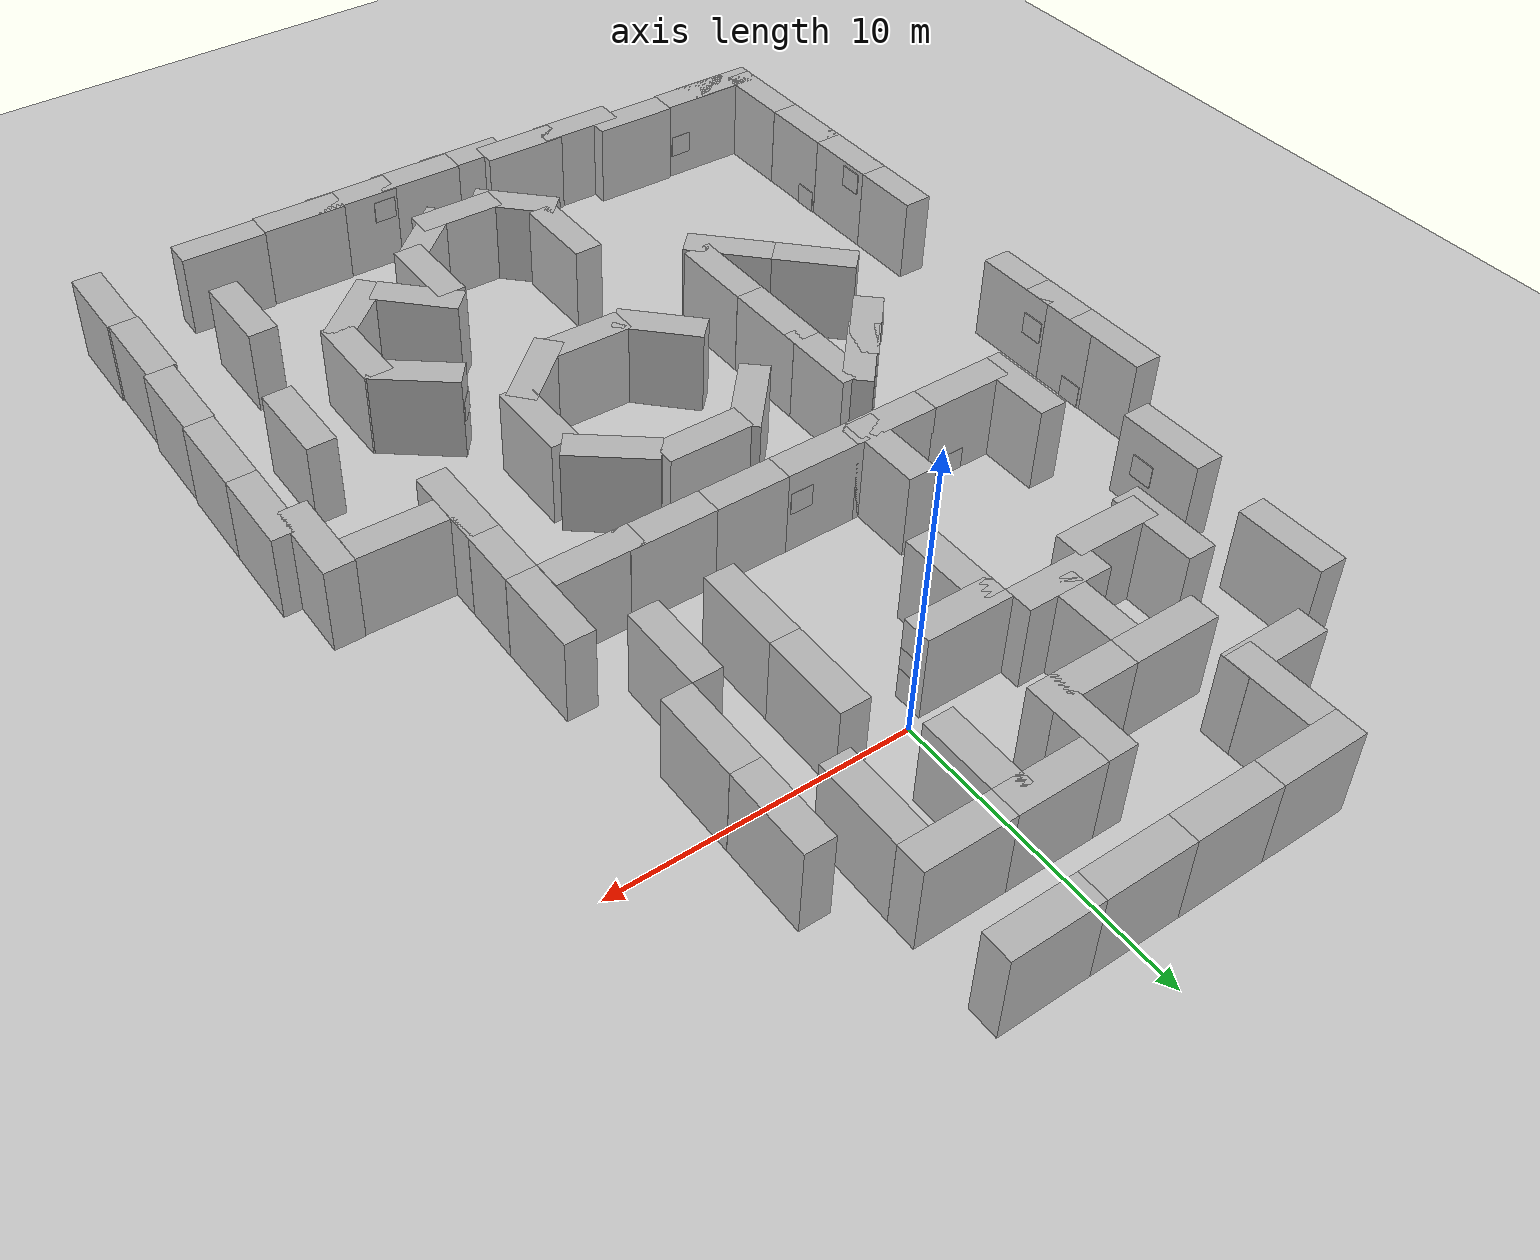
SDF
<sdf version="1.5">
 <world name="default">
  <light name="sun" type="directional">
   <pose>0 0 10 0 -0 0</pose>
   <diffuse>0.8 0.8 0.8 1</diffuse>
   <specular>0.2 0.2 0.2 1</specular>
   <attenuation>
    <range>1000</range>
    <constant>0.9</constant>
    <linear>0.01</linear>
    <quadratic>0.001</quadratic>
   </attenuation>
   <direction>-0.5 0.1 -0.9</direction>
  </light>
  <model name="ground_plane">
   <static>1</static>
   <link name="link">
    <collision name="collision">
     <geometry><plane><normal>0 0 1</normal><size>100 100</size></plane></geometry>
     <surface><friction><ode><mu>100</mu><mu2>50</mu2></ode></friction></surface>
    </collision>
    <visual name="visual">
     <cast_shadows>0</cast_shadows>
     <geometry><plane><normal>0 0 1</normal><size>100 100</size></plane></geometry>
     <material>
      <script><uri>file://media/materials/scripts/gazebo.material</uri><name>Gazebo/Grey</name></script>
     </material>
    </visual>
   </link>
  </model>
  <physics name="default_physics" default="0" type="ode">
   <max_step_size>0.001</max_step_size>
   <real_time_factor>1</real_time_factor>
   <real_time_update_rate>1000</real_time_update_rate>
   <gravity>0 0 -9.8</gravity>
   <magnetic_field>5.5645e-06 2.28758e-05 -4.23884e-05</magnetic_field>
  </physics>
  <scene><ambient>0.4 0.4 0.4 1</ambient><background>0.7 0.7 0.7 1</background><shadows>1</shadows></scene>
  <spherical_coordinates>
   <surface_model>EARTH_WGS84</surface_model>
   <latitude_deg>0</latitude_deg>
   <longitude_deg>0</longitude_deg>
   <elevation>0</elevation>
   <heading_deg>0</heading_deg>
  </spherical_coordinates>
  <model name="brick_box_3x1x3_0">
   <static>1</static>
   <link name="chassis">
    <pose>0 0 1.5 0 -0 0</pose>
    <collision name="collision"><geometry><box><size>3 1 3</size></box></geometry></collision>
    <visual name="visual">
     <geometry><mesh><uri>model://brick_box_3x1x3/meshes/simple_box.dae</uri><scale>3 1 3</scale></mesh></geometry>
     <material>
      <script>
       <uri>model://brick_box_3x1x3/materials/scripts</uri>
       <uri>model://brick_box_3x1x3/materials/textures</uri>
       <name>BrickBox/Diffuse</name>
      </script>
     </material>
    </visual>
   </link>
   <pose>3 8 0 0 -0 0</pose>
  </model>
  <model name="brick_box_3x1x3_1">
   <static>1</static>
   <link name="chassis">
    <pose>0 0 1.5 0 -0 0</pose>
    <collision name="collision"><geometry><box><size>3 1 3</size></box></geometry></collision>
    <visual name="visual">
     <geometry><mesh><uri>model://brick_box_3x1x3/meshes/simple_box.dae</uri><scale>3 1 3</scale></mesh></geometry>
     <material>
      <script>
       <uri>model://brick_box_3x1x3/materials/scripts</uri>
       <uri>model://brick_box_3x1x3/materials/textures</uri>
       <name>BrickBox/Diffuse</name>
      </script>
     </material>
    </visual>
   </link>
   <pose>3 5 0 0 -0 0</pose>
  </model>
  <model name="brick_box_3x1x3_2">
   <static>1</static>
   <link name="chassis">
    <pose>0 0 1.5 0 -0 0</pose>
    <collision name="collision"><geometry><box><size>3 1 3</size></box></geometry></collision>
    <visual name="visual">
     <geometry><mesh><uri>model://brick_box_3x1x3/meshes/simple_box.dae</uri><scale>3 1 3</scale></mesh></geometry>
     <material>
      <script>
       <uri>model://brick_box_3x1x3/materials/scripts</uri>
       <uri>model://brick_box_3x1x3/materials/textures</uri>
       <name>BrickBox/Diffuse</name>
      </script>
     </material>
    </visual>
   </link>
   <pose>0 5 0 0 -0 0</pose>
  </model>
  <model name="brick_box_3x1x3_3">
   <static>1</static>
   <link name="chassis">
    <pose>0 0 1.5 0 -0 0</pose>
    <collision name="collision"><geometry><box><size>3 1 3</size></box></geometry></collision>
    <visual name="visual">
     <geometry><mesh><uri>model://brick_box_3x1x3/meshes/simple_box.dae</uri><scale>3 1 3</scale></mesh></geometry>
     <material>
      <script>
       <uri>model://brick_box_3x1x3/materials/scripts</uri>
       <uri>model://brick_box_3x1x3/materials/textures</uri>
       <name>BrickBox/Diffuse</name>
      </script>
     </material>
    </visual>
   </link>
   <pose>0 8 0 0 -0 0</pose>
  </model>
  <model name="brick_box_3x1x3_4">
   <static>1</static>
   <link name="chassis">
    <pose>0 0 1.5 0 -0 0</pose>
    <collision name="collision"><geometry><box><size>3 1 3</size></box></geometry></collision>
    <visual name="visual">
     <geometry><mesh><uri>model://brick_box_3x1x3/meshes/simple_box.dae</uri><scale>3 1 3</scale></mesh></geometry>
     <material>
      <script>
       <uri>model://brick_box_3x1x3/materials/scripts</uri>
       <uri>model://brick_box_3x1x3/materials/textures</uri>
       <name>BrickBox/Diffuse</name>
      </script>
     </material>
    </visual>
   </link>
   <pose>-3 8 0 0 -0 0</pose>
  </model>
  <model name="brick_box_3x1x3_5">
   <static>1</static>
   <link name="chassis">
    <pose>0 0 1.5 0 -0 0</pose>
    <collision name="collision"><geometry><box><size>3 1 3</size></box></geometry></collision>
    <visual name="visual">
     <geometry><mesh><uri>model://brick_box_3x1x3/meshes/simple_box.dae</uri><scale>3 1 3</scale></mesh></geometry>
     <material>
      <script>
       <uri>model://brick_box_3x1x3/materials/scripts</uri>
       <uri>model://brick_box_3x1x3/materials/textures</uri>
       <name>BrickBox/Diffuse</name>
      </script>
     </material>
    </visual>
   </link>
   <pose>-6 8 0 0 -0 0</pose>
  </model>
  <model name="brick_box_3x1x3_6">
   <static>1</static>
   <link name="chassis">
    <pose>0 0 1.5 0 -0 0</pose>
    <collision name="collision"><geometry><box><size>3 1 3</size></box></geometry></collision>
    <visual name="visual">
     <geometry><mesh><uri>model://brick_box_3x1x3/meshes/simple_box.dae</uri><scale>3 1 3</scale></mesh></geometry>
     <material>
      <script>
       <uri>model://brick_box_3x1x3/materials/scripts</uri>
       <uri>model://brick_box_3x1x3/materials/textures</uri>
       <name>BrickBox/Diffuse</name>
      </script>
     </material>
    </visual>
   </link>
   <pose>-7.00719 6.10957 0 0 -0 1.56927</pose>
  </model>
  <model name="brick_box_3x1x3_6_clone">
   <static>1</static>
   <link name="chassis">
    <pose>0 0 1.5 0 -0 0</pose>
    <collision name="collision"><geometry><box><size>3 1 3</size></box></geometry></collision>
    <visual name="visual">
     <geometry><mesh><uri>model://brick_box_3x1x3/meshes/simple_box.dae</uri><scale>3 1 3</scale></mesh></geometry>
     <material>
      <script>
       <uri>model://brick_box_3x1x3/materials/scripts</uri>
       <uri>model://brick_box_3x1x3/materials/textures</uri>
       <name>BrickBox/Diffuse</name>
      </script>
     </material>
    </visual>
   </link>
   <pose>-2 4 0 0 -0 1.56927</pose>
  </model>
  <model name="brick_box_3x1x3_4_clone">
   <static>1</static>
   <link name="chassis">
    <pose>0 0 1.5 0 -0 0</pose>
    <collision name="collision"><geometry><box><size>3 1 3</size></box></geometry></collision>
    <visual name="visual">
     <geometry><mesh><uri>model://brick_box_3x1x3/meshes/simple_box.dae</uri><scale>3 1 3</scale></mesh></geometry>
     <material>
      <script>
       <uri>model://brick_box_3x1x3/materials/scripts</uri>
       <uri>model://brick_box_3x1x3/materials/textures</uri>
       <name>BrickBox/Diffuse</name>
      </script>
     </material>
    </visual>
   </link>
   <pose>-3 3 0 0 -0 0</pose>
  </model>
  <model name="brick_box_3x1x3_4_clone_clone">
   <static>1</static>
   <link name="chassis">
    <pose>0 0 1.5 0 -0 0</pose>
    <collision name="collision"><geometry><box><size>3 1 3</size></box></geometry></collision>
    <visual name="visual">
     <geometry><mesh><uri>model://brick_box_3x1x3/meshes/simple_box.dae</uri><scale>3 1 3</scale></mesh></geometry>
     <material>
      <script>
       <uri>model://brick_box_3x1x3/materials/scripts</uri>
       <uri>model://brick_box_3x1x3/materials/textures</uri>
       <name>BrickBox/Diffuse</name>
      </script>
     </material>
    </visual>
   </link>
   <pose>-8 5 0 0 -0 0</pose>
  </model>
  <model name="brick_box_3x1x3_4_clone_clone_0">
   <static>1</static>
   <link name="chassis">
    <pose>0 0 1.5 0 -0 0</pose>
    <collision name="collision"><geometry><box><size>3 1 3</size></box></geometry></collision>
    <visual name="visual">
     <geometry><mesh><uri>model://brick_box_3x1x3/meshes/simple_box.dae</uri><scale>3 1 3</scale></mesh></geometry>
     <material>
      <script>
       <uri>model://brick_box_3x1x3/materials/scripts</uri>
       <uri>model://brick_box_3x1x3/materials/textures</uri>
       <name>BrickBox/Diffuse</name>
      </script>
     </material>
    </visual>
   </link>
   <pose>-6 3 0 0 -0 0</pose>
  </model>
  <model name="brick_box_3x1x3_1_clone">
   <static>1</static>
   <link name="chassis">
    <pose>0 0 1.5 0 -0 0</pose>
    <collision name="collision"><geometry><box><size>3 1 3</size></box></geometry></collision>
    <visual name="visual">
     <geometry><mesh><uri>model://brick_box_3x1x3/meshes/simple_box.dae</uri><scale>3 1 3</scale></mesh></geometry>
     <material>
      <script>
       <uri>model://brick_box_3x1x3/materials/scripts</uri>
       <uri>model://brick_box_3x1x3/materials/textures</uri>
       <name>BrickBox/Diffuse</name>
      </script>
     </material>
    </visual>
   </link>
   <pose>-7.61871 -0.795439 0 0 -0 0</pose>
  </model>
  <model name="brick_box_3x1x3_1_clone_clone">
   <static>1</static>
   <link name="chassis">
    <pose>0 0 1.5 0 -0 0</pose>
    <collision name="collision"><geometry><box><size>3 1 3</size></box></geometry></collision>
    <visual name="visual">
     <geometry><mesh><uri>model://brick_box_3x1x3/meshes/simple_box.dae</uri><scale>3 1 3</scale></mesh></geometry>
     <material>
      <script>
       <uri>model://brick_box_3x1x3/materials/scripts</uri>
       <uri>model://brick_box_3x1x3/materials/textures</uri>
       <name>BrickBox/Diffuse</name>
      </script>
     </material>
    </visual>
   </link>
   <pose>-5 0 0 0 -0 0</pose>
  </model>
  <model name="brick_box_3x1x3_1_clone_clone_clone">
   <static>1</static>
   <link name="chassis">
    <pose>0 0 1.5 0 -0 0</pose>
    <collision name="collision"><geometry><box><size>3 1 3</size></box></geometry></collision>
    <visual name="visual">
     <geometry><mesh><uri>model://brick_box_3x1x3/meshes/simple_box.dae</uri><scale>3 1 3</scale></mesh></geometry>
     <material>
      <script>
       <uri>model://brick_box_3x1x3/materials/scripts</uri>
       <uri>model://brick_box_3x1x3/materials/textures</uri>
       <name>BrickBox/Diffuse</name>
      </script>
     </material>
    </visual>
   </link>
   <pose>-2 -0.680933 0 0 -0 0</pose>
  </model>
  <model name="brick_box_3x1x3_6_clone_0">
   <static>1</static>
   <link name="chassis">
    <pose>0 0 1.5 0 -0 0</pose>
    <collision name="collision"><geometry><box><size>3 1 3</size></box></geometry></collision>
    <visual name="visual">
     <geometry><mesh><uri>model://brick_box_3x1x3/meshes/simple_box.dae</uri><scale>3 1 3</scale></mesh></geometry>
     <material>
      <script>
       <uri>model://brick_box_3x1x3/materials/scripts</uri>
       <uri>model://brick_box_3x1x3/materials/textures</uri>
       <name>BrickBox/Diffuse</name>
      </script>
     </material>
    </visual>
   </link>
   <pose>-5 1.49506 0 0 -0 1.56927</pose>
  </model>
  <model name="brick_box_3x1x3_6_clone_0_clone">
   <static>1</static>
   <link name="chassis">
    <pose>0 0 1.5 0 -0 0</pose>
    <collision name="collision"><geometry><box><size>3 1 3</size></box></geometry></collision>
    <visual name="visual">
     <geometry><mesh><uri>model://brick_box_3x1x3/meshes/simple_box.dae</uri><scale>3 1 3</scale></mesh></geometry>
     <material>
      <script>
       <uri>model://brick_box_3x1x3/materials/scripts</uri>
       <uri>model://brick_box_3x1x3/materials/textures</uri>
       <name>BrickBox/Diffuse</name>
      </script>
     </material>
    </visual>
   </link>
   <pose>1 3.42288 0 0 -0 1.56927</pose>
  </model>
  <model name="brick_box_3x1x3_6_clone_1">
   <static>1</static>
   <link name="chassis">
    <pose>0 0 1.5 0 -0 0</pose>
    <collision name="collision"><geometry><box><size>3 1 3</size></box></geometry></collision>
    <visual name="visual">
     <geometry><mesh><uri>model://brick_box_3x1x3/meshes/simple_box.dae</uri><scale>3 1 3</scale></mesh></geometry>
     <material>
      <script>
       <uri>model://brick_box_3x1x3/materials/scripts</uri>
       <uri>model://brick_box_3x1x3/materials/textures</uri>
       <name>BrickBox/Diffuse</name>
      </script>
     </material>
    </visual>
   </link>
   <pose>-9 0 0 0 -0 1.56927</pose>
  </model>
  <model name="brick_box_3x1x3_6_clone_2">
   <static>1</static>
   <link name="chassis">
    <pose>0 0 1.5 0 -0 0</pose>
    <collision name="collision"><geometry><box><size>3 1 3</size></box></geometry></collision>
    <visual name="visual">
     <geometry><mesh><uri>model://brick_box_3x1x3/meshes/simple_box.dae</uri><scale>3 1 3</scale></mesh></geometry>
     <material>
      <script>
       <uri>model://brick_box_3x1x3/materials/scripts</uri>
       <uri>model://brick_box_3x1x3/materials/textures</uri>
       <name>BrickBox/Diffuse</name>
      </script>
     </material>
    </visual>
   </link>
   <pose>4 3 0 0 -0 1.56927</pose>
  </model>
  <model name="brick_box_3x1x3_1_clone_clone_clone_clone_clone">
   <static>1</static>
   <link name="chassis">
    <pose>0 0 1.5 0 -0 0</pose>
    <collision name="collision"><geometry><box><size>3 1 3</size></box></geometry></collision>
    <visual name="visual">
     <geometry><mesh><uri>model://brick_box_3x1x3/meshes/simple_box.dae</uri><scale>3 1 3</scale></mesh></geometry>
     <material>
      <script>
       <uri>model://brick_box_3x1x3/materials/scripts</uri>
       <uri>model://brick_box_3x1x3/materials/textures</uri>
       <name>BrickBox/Diffuse</name>
      </script>
     </material>
    </visual>
   </link>
   <pose>-8.49587 -8 0 0 -0 0</pose>
  </model>
  <model name="brick_box_3x1x3_1_clone_clone_clone_clone_clone_0">
   <static>1</static>
   <link name="chassis">
    <pose>0 0 1.5 0 -0 0</pose>
    <collision name="collision"><geometry><box><size>3 1 3</size></box></geometry></collision>
    <visual name="visual">
     <geometry><mesh><uri>model://brick_box_3x1x3/meshes/simple_box.dae</uri><scale>3 1 3</scale></mesh></geometry>
     <material>
      <script>
       <uri>model://brick_box_3x1x3/materials/scripts</uri>
       <uri>model://brick_box_3x1x3/materials/textures</uri>
       <name>BrickBox/Diffuse</name>
      </script>
     </material>
    </visual>
   </link>
   <pose>-5.55806 -8 0 0 -0 0</pose>
  </model>
  <model name="brick_box_3x1x3_1_clone_clone_clone_clone_clone_1">
   <static>1</static>
   <link name="chassis">
    <pose>0 0 1.5 0 -0 0</pose>
    <collision name="collision"><geometry><box><size>3 1 3</size></box></geometry></collision>
    <visual name="visual">
     <geometry><mesh><uri>model://brick_box_3x1x3/meshes/simple_box.dae</uri><scale>3 1 3</scale></mesh></geometry>
     <material>
      <script>
       <uri>model://brick_box_3x1x3/materials/scripts</uri>
       <uri>model://brick_box_3x1x3/materials/textures</uri>
       <name>BrickBox/Diffuse</name>
      </script>
     </material>
    </visual>
   </link>
   <pose>-3 -8 0 0 -0 0</pose>
  </model>
  <model name="brick_box_3x1x3_1_clone_clone_clone_clone_clone_2">
   <static>1</static>
   <link name="chassis">
    <pose>0 0 1.5 0 -0 0</pose>
    <collision name="collision"><geometry><box><size>3 1 3</size></box></geometry></collision>
    <visual name="visual">
     <geometry><mesh><uri>model://brick_box_3x1x3/meshes/simple_box.dae</uri><scale>3 1 3</scale></mesh></geometry>
     <material>
      <script>
       <uri>model://brick_box_3x1x3/materials/scripts</uri>
       <uri>model://brick_box_3x1x3/materials/textures</uri>
       <name>BrickBox/Diffuse</name>
      </script>
     </material>
    </visual>
   </link>
   <pose>-0.433734 -8 0 0 -0 0</pose>
  </model>
  <model name="brick_box_3x1x3_1_clone_clone_clone_clone_clone_3">
   <static>1</static>
   <link name="chassis">
    <pose>0 0 1.5 0 -0 0</pose>
    <collision name="collision"><geometry><box><size>3 1 3</size></box></geometry></collision>
    <visual name="visual">
     <geometry><mesh><uri>model://brick_box_3x1x3/meshes/simple_box.dae</uri><scale>3 1 3</scale></mesh></geometry>
     <material>
      <script>
       <uri>model://brick_box_3x1x3/materials/scripts</uri>
       <uri>model://brick_box_3x1x3/materials/textures</uri>
       <name>BrickBox/Diffuse</name>
      </script>
     </material>
    </visual>
   </link>
   <pose>2.54551 -8 0 0 -0 0</pose>
  </model>
  <model name="brick_box_3x1x3_1_clone_clone_clone_clone_clone_4">
   <static>1</static>
   <link name="chassis">
    <pose>0 0 1.5 0 -0 0</pose>
    <collision name="collision"><geometry><box><size>3 1 3</size></box></geometry></collision>
    <visual name="visual">
     <geometry><mesh><uri>model://brick_box_3x1x3/meshes/simple_box.dae</uri><scale>3 1 3</scale></mesh></geometry>
     <material>
      <script>
       <uri>model://brick_box_3x1x3/materials/scripts</uri>
       <uri>model://brick_box_3x1x3/materials/textures</uri>
       <name>BrickBox/Diffuse</name>
      </script>
     </material>
    </visual>
   </link>
   <pose>4.98932 -8.01047 0 0 -0 0</pose>
  </model>
  <model name="brick_box_3x1x3_6_clone_0_clone_0">
   <static>1</static>
   <link name="chassis">
    <pose>0 0 1.5 0 -0 0</pose>
    <collision name="collision"><geometry><box><size>3 1 3</size></box></geometry></collision>
    <visual name="visual">
     <geometry><mesh><uri>model://brick_box_3x1x3/meshes/simple_box.dae</uri><scale>3 1 3</scale></mesh></geometry>
     <material>
      <script>
       <uri>model://brick_box_3x1x3/materials/scripts</uri>
       <uri>model://brick_box_3x1x3/materials/textures</uri>
       <name>BrickBox/Diffuse</name>
      </script>
     </material>
    </visual>
   </link>
   <pose>-4.78193 -6.92335 0 0 -0 1.56927</pose>
  </model>
  <model name="brick_box_3x1x3_6_clone_0_clone_1">
   <static>1</static>
   <link name="chassis">
    <pose>0 0 1.5 0 -0 0</pose>
    <collision name="collision"><geometry><box><size>3 1 3</size></box></geometry></collision>
    <visual name="visual">
     <geometry><mesh><uri>model://brick_box_3x1x3/meshes/simple_box.dae</uri><scale>3 1 3</scale></mesh></geometry>
     <material>
      <script>
       <uri>model://brick_box_3x1x3/materials/scripts</uri>
       <uri>model://brick_box_3x1x3/materials/textures</uri>
       <name>BrickBox/Diffuse</name>
      </script>
     </material>
    </visual>
   </link>
   <pose>-3 -2 0 0 -0 1.56927</pose>
  </model>
  <model name="brick_box_3x1x3_6_clone_0_clone_2">
   <static>1</static>
   <link name="chassis">
    <pose>0 0 1.5 0 -0 0</pose>
    <collision name="collision"><geometry><box><size>3 1 3</size></box></geometry></collision>
    <visual name="visual">
     <geometry><mesh><uri>model://brick_box_3x1x3/meshes/simple_box.dae</uri><scale>3 1 3</scale></mesh></geometry>
     <material>
      <script>
       <uri>model://brick_box_3x1x3/materials/scripts</uri>
       <uri>model://brick_box_3x1x3/materials/textures</uri>
       <name>BrickBox/Diffuse</name>
      </script>
     </material>
    </visual>
   </link>
   <pose>2.50019 -1 0 0 -0 1.56927</pose>
  </model>
  <model name="brick_box_3x1x3_6_clone_0_clone_3">
   <static>1</static>
   <link name="chassis">
    <pose>0 0 1.5 0 -0 0</pose>
    <collision name="collision"><geometry><box><size>3 1 3</size></box></geometry></collision>
    <visual name="visual">
     <geometry><mesh><uri>model://brick_box_3x1x3/meshes/simple_box.dae</uri><scale>3 1 3</scale></mesh></geometry>
     <material>
      <script>
       <uri>model://brick_box_3x1x3/materials/scripts</uri>
       <uri>model://brick_box_3x1x3/materials/textures</uri>
       <name>BrickBox/Diffuse</name>
      </script>
     </material>
    </visual>
   </link>
   <pose>2.48978 -4 0 0 -0 1.56927</pose>
  </model>
  <model name="brick_box_3x1x3_6_clone_0_clone_4">
   <static>1</static>
   <link name="chassis">
    <pose>0 0 1.5 0 -0 0</pose>
    <collision name="collision"><geometry><box><size>3 1 3</size></box></geometry></collision>
    <visual name="visual">
     <geometry><mesh><uri>model://brick_box_3x1x3/meshes/simple_box.dae</uri><scale>3 1 3</scale></mesh></geometry>
     <material>
      <script>
       <uri>model://brick_box_3x1x3/materials/scripts</uri>
       <uri>model://brick_box_3x1x3/materials/textures</uri>
       <name>BrickBox/Diffuse</name>
      </script>
     </material>
    </visual>
   </link>
   <pose>5 -4 0 0 -0 1.56927</pose>
  </model>
  <model name="brick_box_3x1x3_6_clone_0_clone_5">
   <static>1</static>
   <link name="chassis">
    <pose>0 0 1.5 0 -0 0</pose>
    <collision name="collision"><geometry><box><size>3 1 3</size></box></geometry></collision>
    <visual name="visual">
     <geometry><mesh><uri>model://brick_box_3x1x3/meshes/simple_box.dae</uri><scale>3 1 3</scale></mesh></geometry>
     <material>
      <script>
       <uri>model://brick_box_3x1x3/materials/scripts</uri>
       <uri>model://brick_box_3x1x3/materials/textures</uri>
       <name>BrickBox/Diffuse</name>
      </script>
     </material>
    </visual>
   </link>
   <pose>6 -1 0 0 -0 1.56927</pose>
  </model>
  <model name="brick_box_3x1x3_6_clone_0_clone_6">
   <static>1</static>
   <link name="chassis">
    <pose>0 0 1.5 0 -0 0</pose>
    <collision name="collision"><geometry><box><size>3 1 3</size></box></geometry></collision>
    <visual name="visual">
     <geometry><mesh><uri>model://brick_box_3x1x3/meshes/simple_box.dae</uri><scale>3 1 3</scale></mesh></geometry>
     <material>
      <script>
       <uri>model://brick_box_3x1x3/materials/scripts</uri>
       <uri>model://brick_box_3x1x3/materials/textures</uri>
       <name>BrickBox/Diffuse</name>
      </script>
     </material>
    </visual>
   </link>
   <pose>6 2 0 0 -0 1.56927</pose>
  </model>
  <model name="brick_box_3x1x3_6_clone_0_clone_6_clone">
   <static>1</static>
   <link name="chassis">
    <pose>0 0 1.5 0 -0 0</pose>
    <collision name="collision"><geometry><box><size>3 1 3</size></box></geometry></collision>
    <visual name="visual">
     <geometry><mesh><uri>model://brick_box_3x1x3/meshes/simple_box.dae</uri><scale>3 1 3</scale></mesh></geometry>
     <material>
      <script>
       <uri>model://brick_box_3x1x3/materials/scripts</uri>
       <uri>model://brick_box_3x1x3/materials/textures</uri>
       <name>BrickBox/Diffuse</name>
      </script>
     </material>
    </visual>
   </link>
   <pose>7 -7 0 0 -0 1.56927</pose>
  </model>
  <model name="brick_box_3x1x3_6_clone_0_clone_6_clone_clone">
   <static>1</static>
   <link name="chassis">
    <pose>0 0 1.5 0 -0 0</pose>
    <collision name="collision"><geometry><box><size>3 1 3</size></box></geometry></collision>
    <visual name="visual">
     <geometry><mesh><uri>model://brick_box_3x1x3/meshes/simple_box.dae</uri><scale>3 1 3</scale></mesh></geometry>
     <material>
      <script>
       <uri>model://brick_box_3x1x3/materials/scripts</uri>
       <uri>model://brick_box_3x1x3/materials/textures</uri>
       <name>BrickBox/Diffuse</name>
      </script>
     </material>
    </visual>
   </link>
   <pose>-10 -7 0 0 -0 1.56927</pose>
  </model>
  <model name="brick_box_3x1x3_6_clone_0_clone_6_clone_clone_0">
   <static>1</static>
   <link name="chassis">
    <pose>0 0 1.5 0 -0 0</pose>
    <collision name="collision"><geometry><box><size>3 1 3</size></box></geometry></collision>
    <visual name="visual">
     <geometry><mesh><uri>model://brick_box_3x1x3/meshes/simple_box.dae</uri><scale>3 1 3</scale></mesh></geometry>
     <material>
      <script>
       <uri>model://brick_box_3x1x3/materials/scripts</uri>
       <uri>model://brick_box_3x1x3/materials/textures</uri>
       <name>BrickBox/Diffuse</name>
      </script>
     </material>
    </visual>
   </link>
   <pose>-12 -2.55136 0 0 -0 1.56927</pose>
  </model>
  <model name="brick_box_3x1x3_6_clone_0_clone_6_clone_clone_0_clone">
   <static>1</static>
   <link name="chassis">
    <pose>0 0 1.5 0 -0 0</pose>
    <collision name="collision"><geometry><box><size>3 1 3</size></box></geometry></collision>
    <visual name="visual">
     <geometry><mesh><uri>model://brick_box_3x1x3/meshes/simple_box.dae</uri><scale>3 1 3</scale></mesh></geometry>
     <material>
      <script>
       <uri>model://brick_box_3x1x3/materials/scripts</uri>
       <uri>model://brick_box_3x1x3/materials/textures</uri>
       <name>BrickBox/Diffuse</name>
      </script>
     </material>
    </visual>
   </link>
   <pose>-11.5925 2.40821 0 0 -0 1.56927</pose>
  </model>
  <model name="brick_box_3x1x3_6_clone_0_clone_6_clone_clone_0_clone_0">
   <static>1</static>
   <link name="chassis">
    <pose>0 0 1.5 0 -0 0</pose>
    <collision name="collision"><geometry><box><size>3 1 3</size></box></geometry></collision>
    <visual name="visual">
     <geometry><mesh><uri>model://brick_box_3x1x3/meshes/simple_box.dae</uri><scale>3 1 3</scale></mesh></geometry>
     <material>
      <script>
       <uri>model://brick_box_3x1x3/materials/scripts</uri>
       <uri>model://brick_box_3x1x3/materials/textures</uri>
       <name>BrickBox/Diffuse</name>
      </script>
     </material>
    </visual>
   </link>
   <pose>-2.81968 -11.2135 -0 0 -0 0.824357</pose>
  </model>
  <model name="brick_box_3x1x3_6_clone_0_clone_6_clone_clone_0_clone_0_clone">
   <static>1</static>
   <link name="chassis">
    <pose>0 0 1.5 0 -0 0</pose>
    <collision name="collision"><geometry><box><size>3 1 3</size></box></geometry></collision>
    <visual name="visual">
     <geometry><mesh><uri>model://brick_box_3x1x3/meshes/simple_box.dae</uri><scale>3 1 3</scale></mesh></geometry>
     <material>
      <script>
       <uri>model://brick_box_3x1x3/materials/scripts</uri>
       <uri>model://brick_box_3x1x3/materials/textures</uri>
       <name>BrickBox/Diffuse</name>
      </script>
     </material>
    </visual>
   </link>
   <pose>-2.64043 -15.7624 0 0 -0 2.35483</pose>
  </model>
  <model name="brick_box_3x1x3_6_clone_0_clone_6_clone_clone_0_clone_0_clone_clone">
   <static>1</static>
   <link name="chassis">
    <pose>0 0 1.5 0 -0 0</pose>
    <collision name="collision"><geometry><box><size>3 1 3</size></box></geometry></collision>
    <visual name="visual">
     <geometry><mesh><uri>model://brick_box_3x1x3/meshes/simple_box.dae</uri><scale>3 1 3</scale></mesh></geometry>
     <material>
      <script>
       <uri>model://brick_box_3x1x3/materials/scripts</uri>
       <uri>model://brick_box_3x1x3/materials/textures</uri>
       <name>BrickBox/Diffuse</name>
      </script>
     </material>
    </visual>
   </link>
   <pose>-0.268058 -16.5959 0 0 -0 3.11976</pose>
  </model>
  <model name="brick_box_3x1x3_6_clone_0_clone_6_clone_clone_0_clone_0_clone_clone_0">
   <static>1</static>
   <link name="chassis">
    <pose>0 0 1.5 0 -0 0</pose>
    <collision name="collision"><geometry><box><size>3 1 3</size></box></geometry></collision>
    <visual name="visual">
     <geometry><mesh><uri>model://brick_box_3x1x3/meshes/simple_box.dae</uri><scale>3 1 3</scale></mesh></geometry>
     <material>
      <script>
       <uri>model://brick_box_3x1x3/materials/scripts</uri>
       <uri>model://brick_box_3x1x3/materials/textures</uri>
       <name>BrickBox/Diffuse</name>
      </script>
     </material>
    </visual>
   </link>
   <pose>-0.541851 -10.4768 0 0 0 -0.007092</pose>
  </model>
  <model name="brick_box_3x1x3_6_clone_0_clone_6_clone_clone_0_clone_0_clone_clone_1">
   <static>1</static>
   <link name="chassis">
    <pose>0 0 1.5 0 -0 0</pose>
    <collision name="collision"><geometry><box><size>3 1 3</size></box></geometry></collision>
    <visual name="visual">
     <geometry><mesh><uri>model://brick_box_3x1x3/meshes/simple_box.dae</uri><scale>3 1 3</scale></mesh></geometry>
     <material>
      <script>
       <uri>model://brick_box_3x1x3/materials/scripts</uri>
       <uri>model://brick_box_3x1x3/materials/textures</uri>
       <name>BrickBox/Diffuse</name>
      </script>
     </material>
    </visual>
   </link>
   <pose>3 -14 0 0 -0 1.56927</pose>
  </model>
  <model name="brick_box_3x1x3_6_clone_0_clone_6_clone_clone_0_clone_0_clone_clone_2">
   <static>1</static>
   <link name="chassis">
    <pose>0 0 1.5 0 -0 0</pose>
    <collision name="collision"><geometry><box><size>3 1 3</size></box></geometry></collision>
    <visual name="visual">
     <geometry><mesh><uri>model://brick_box_3x1x3/meshes/simple_box.dae</uri><scale>3 1 3</scale></mesh></geometry>
     <material>
      <script>
       <uri>model://brick_box_3x1x3/materials/scripts</uri>
       <uri>model://brick_box_3x1x3/materials/textures</uri>
       <name>BrickBox/Diffuse</name>
      </script>
     </material>
    </visual>
   </link>
   <pose>2 -11.5506 -0 0 -0 2.47586</pose>
  </model>
  <model name="brick_box_3x1x3_6_clone_0_clone_6_clone_clone_0_clone_0_clone_clone_3">
   <static>1</static>
   <link name="chassis">
    <pose>0 0 1.5 0 -0 0</pose>
    <collision name="collision"><geometry><box><size>3 1 3</size></box></geometry></collision>
    <visual name="visual">
     <geometry><mesh><uri>model://brick_box_3x1x3/meshes/simple_box.dae</uri><scale>3 1 3</scale></mesh></geometry>
     <material>
      <script>
       <uri>model://brick_box_3x1x3/materials/scripts</uri>
       <uri>model://brick_box_3x1x3/materials/textures</uri>
       <name>BrickBox/Diffuse</name>
      </script>
     </material>
    </visual>
   </link>
   <pose>1.8811 -16.0067 0 0 -0 0.719961</pose>
  </model>
  <model name="brick_box_3x1x3_6_clone_0_clone_6_clone_clone_0_clone_0_clone_clone_4">
   <static>1</static>
   <link name="chassis">
    <pose>0 0 1.5 0 -0 0</pose>
    <collision name="collision"><geometry><box><size>3 1 3</size></box></geometry></collision>
    <visual name="visual">
     <geometry><mesh><uri>model://brick_box_3x1x3/meshes/simple_box.dae</uri><scale>3 1 3</scale></mesh></geometry>
     <material>
      <script>
       <uri>model://brick_box_3x1x3/materials/scripts</uri>
       <uri>model://brick_box_3x1x3/materials/textures</uri>
       <name>BrickBox/Diffuse</name>
      </script>
     </material>
    </visual>
   </link>
   <pose>-9 -16 0 0 -0 2.35483</pose>
  </model>
  <model name="brick_box_3x1x3_6_clone_0_clone_6_clone_clone_0_clone_0_clone_clone_5">
   <static>1</static>
   <link name="chassis">
    <pose>0 0 1.5 0 -0 0</pose>
    <collision name="collision"><geometry><box><size>3 1 3</size></box></geometry></collision>
    <visual name="visual">
     <geometry><mesh><uri>model://brick_box_3x1x3/meshes/simple_box.dae</uri><scale>3 1 3</scale></mesh></geometry>
     <material>
      <script>
       <uri>model://brick_box_3x1x3/materials/scripts</uri>
       <uri>model://brick_box_3x1x3/materials/textures</uri>
       <name>BrickBox/Diffuse</name>
      </script>
     </material>
    </visual>
   </link>
   <pose>-7 -18 0 0 -0 2.35483</pose>
  </model>
  <model name="brick_box_3x1x3_6_clone_0_clone_6_clone_clone_0_clone_0_clone_clone_1_clone">
   <static>1</static>
   <link name="chassis">
    <pose>0 0 1.5 0 -0 0</pose>
    <collision name="collision"><geometry><box><size>3 1 3</size></box></geometry></collision>
    <visual name="visual">
     <geometry><mesh><uri>model://brick_box_3x1x3/meshes/simple_box.dae</uri><scale>3 1 3</scale></mesh></geometry>
     <material>
      <script>
       <uri>model://brick_box_3x1x3/materials/scripts</uri>
       <uri>model://brick_box_3x1x3/materials/textures</uri>
       <name>BrickBox/Diffuse</name>
      </script>
     </material>
    </visual>
   </link>
   <pose>-6 -17 0 0 -0 1.56927</pose>
  </model>
  <model name="brick_box_3x1x3_6_clone_0_clone_6_clone_clone_0_clone_0_clone_clone_1_clone_0">
   <static>1</static>
   <link name="chassis">
    <pose>0 0 1.5 0 -0 0</pose>
    <collision name="collision"><geometry><box><size>3 1 3</size></box></geometry></collision>
    <visual name="visual">
     <geometry><mesh><uri>model://brick_box_3x1x3/meshes/simple_box.dae</uri><scale>3 1 3</scale></mesh></geometry>
     <material>
      <script>
       <uri>model://brick_box_3x1x3/materials/scripts</uri>
       <uri>model://brick_box_3x1x3/materials/textures</uri>
       <name>BrickBox/Diffuse</name>
      </script>
     </material>
    </visual>
   </link>
   <pose>-6 -14 0 0 -0 1.56927</pose>
  </model>
  <model name="brick_box_3x1x3_6_clone_0_clone_6_clone_clone_0_clone_0_clone_clone_1_clone_1">
   <static>1</static>
   <link name="chassis">
    <pose>0 0 1.5 0 -0 0</pose>
    <collision name="collision"><geometry><box><size>3 1 3</size></box></geometry></collision>
    <visual name="visual">
     <geometry><mesh><uri>model://brick_box_3x1x3/meshes/simple_box.dae</uri><scale>3 1 3</scale></mesh></geometry>
     <material>
      <script>
       <uri>model://brick_box_3x1x3/materials/scripts</uri>
       <uri>model://brick_box_3x1x3/materials/textures</uri>
       <name>BrickBox/Diffuse</name>
      </script>
     </material>
    </visual>
   </link>
   <pose>-6 -11.5224 0 0 -0 1.56927</pose>
  </model>
  <model name="brick_box_3x1x3_6_clone_0_clone_6_clone_clone_0_clone_0_clone_0">
   <static>1</static>
   <link name="chassis">
    <pose>0 0 1.5 0 -0 0</pose>
    <collision name="collision"><geometry><box><size>3 1 3</size></box></geometry></collision>
    <visual name="visual">
     <geometry><mesh><uri>model://brick_box_3x1x3/meshes/simple_box.dae</uri><scale>3 1 3</scale></mesh></geometry>
     <material>
      <script>
       <uri>model://brick_box_3x1x3/materials/scripts</uri>
       <uri>model://brick_box_3x1x3/materials/textures</uri>
       <name>BrickBox/Diffuse</name>
      </script>
     </material>
    </visual>
   </link>
   <pose>-7 -11 -0 0 -0 0.824357</pose>
  </model>
  <model name="brick_box_3x1x3_6_clone_0_clone_6_clone_clone_0_clone_0_clone_0_clone">
   <static>1</static>
   <link name="chassis">
    <pose>0 0 1.5 0 -0 0</pose>
    <collision name="collision"><geometry><box><size>3 1 3</size></box></geometry></collision>
    <visual name="visual">
     <geometry><mesh><uri>model://brick_box_3x1x3/meshes/simple_box.dae</uri><scale>3 1 3</scale></mesh></geometry>
     <material>
      <script>
       <uri>model://brick_box_3x1x3/materials/scripts</uri>
       <uri>model://brick_box_3x1x3/materials/textures</uri>
       <name>BrickBox/Diffuse</name>
      </script>
     </material>
    </visual>
   </link>
   <pose>-8 -12 -0 0 -0 0.824357</pose>
  </model>
  <model name="brick_box_3x1x3_6_clone_0_clone_6_clone_clone_0_clone_0_clone_clone_clone">
   <static>1</static>
   <link name="chassis">
    <pose>0 0 1.5 0 -0 0</pose>
    <collision name="collision"><geometry><box><size>3 1 3</size></box></geometry></collision>
    <visual name="visual">
     <geometry><mesh><uri>model://brick_box_3x1x3/meshes/simple_box.dae</uri><scale>3 1 3</scale></mesh></geometry>
     <material>
      <script>
       <uri>model://brick_box_3x1x3/materials/scripts</uri>
       <uri>model://brick_box_3x1x3/materials/textures</uri>
       <name>BrickBox/Diffuse</name>
      </script>
     </material>
    </visual>
   </link>
   <pose>-0.519279 -25 0 0 -0 3.11976</pose>
  </model>
  <model name="brick_box_3x1x3_6_clone_0_clone_6_clone_clone_0_clone_0_clone_clone_6">
   <static>1</static>
   <link name="chassis">
    <pose>0 0 1.5 0 -0 0</pose>
    <collision name="collision"><geometry><box><size>3 1 3</size></box></geometry></collision>
    <visual name="visual">
     <geometry><mesh><uri>model://brick_box_3x1x3/meshes/simple_box.dae</uri><scale>3 1 3</scale></mesh></geometry>
     <material>
      <script>
       <uri>model://brick_box_3x1x3/materials/scripts</uri>
       <uri>model://brick_box_3x1x3/materials/textures</uri>
       <name>BrickBox/Diffuse</name>
      </script>
     </material>
    </visual>
   </link>
   <pose>-2.48318 -24.4414 0 0 -0 2.35483</pose>
  </model>
  <model name="brick_box_3x1x3_6_clone_0_clone_6_clone_clone_0_clone_0_clone_clone_1_clone_2">
   <static>1</static>
   <link name="chassis">
    <pose>0 0 1.5 0 -0 0</pose>
    <collision name="collision"><geometry><box><size>3 1 3</size></box></geometry></collision>
    <visual name="visual">
     <geometry><mesh><uri>model://brick_box_3x1x3/meshes/simple_box.dae</uri><scale>3 1 3</scale></mesh></geometry>
     <material>
      <script>
       <uri>model://brick_box_3x1x3/materials/scripts</uri>
       <uri>model://brick_box_3x1x3/materials/textures</uri>
       <name>BrickBox/Diffuse</name>
      </script>
     </material>
    </visual>
   </link>
   <pose>-3 -22 0 0 -0 1.56927</pose>
  </model>
  <model name="brick_box_3x1x3_6_clone_0_clone_6_clone_clone_0_clone_0_clone_clone_3_clone">
   <static>1</static>
   <link name="chassis">
    <pose>0 0 1.5 0 -0 0</pose>
    <collision name="collision"><geometry><box><size>3 1 3</size></box></geometry></collision>
    <visual name="visual">
     <geometry><mesh><uri>model://brick_box_3x1x3/meshes/simple_box.dae</uri><scale>3 1 3</scale></mesh></geometry>
     <material>
      <script>
       <uri>model://brick_box_3x1x3/materials/scripts</uri>
       <uri>model://brick_box_3x1x3/materials/textures</uri>
       <name>BrickBox/Diffuse</name>
      </script>
     </material>
    </visual>
   </link>
   <pose>1 -24.4534 0 0 -0 0.719961</pose>
  </model>
  <model name="brick_box_3x1x3_6_clone_0_clone_6_clone_clone_0_clone_0_clone_clone_1_clone_2_clone">
   <static>1</static>
   <link name="chassis">
    <pose>0 0 1.5 0 -0 0</pose>
    <collision name="collision"><geometry><box><size>3 1 3</size></box></geometry></collision>
    <visual name="visual">
     <geometry><mesh><uri>model://brick_box_3x1x3/meshes/simple_box.dae</uri><scale>3 1 3</scale></mesh></geometry>
     <material>
      <script>
       <uri>model://brick_box_3x1x3/materials/scripts</uri>
       <uri>model://brick_box_3x1x3/materials/textures</uri>
       <name>BrickBox/Diffuse</name>
      </script>
     </material>
    </visual>
   </link>
   <pose>2 -22.4741 0 0 -0 1.56927</pose>
  </model>
  <model name="brick_box_3x1x3_6_clone_0_clone_6_clone_clone_0_clone_0_clone_clone_6_clone">
   <static>1</static>
   <link name="chassis">
    <pose>0 0 1.5 0 -0 0</pose>
    <collision name="collision"><geometry><box><size>3 1 3</size></box></geometry></collision>
    <visual name="visual">
     <geometry><mesh><uri>model://brick_box_3x1x3/meshes/simple_box.dae</uri><scale>3 1 3</scale></mesh></geometry>
     <material>
      <script>
       <uri>model://brick_box_3x1x3/materials/scripts</uri>
       <uri>model://brick_box_3x1x3/materials/textures</uri>
       <name>BrickBox/Diffuse</name>
      </script>
     </material>
    </visual>
   </link>
   <pose>3 -21.4598 0 0 -0 2.35483</pose>
  </model>
  <model name="brick_box_3x1x3_6_clone_0_clone_6_clone_clone_0_clone_0_clone_clone_3_clone_clone">
   <static>1</static>
   <link name="chassis">
    <pose>0 0 1.5 0 -0 0</pose>
    <collision name="collision"><geometry><box><size>3 1 3</size></box></geometry></collision>
    <visual name="visual">
     <geometry><mesh><uri>model://brick_box_3x1x3/meshes/simple_box.dae</uri><scale>3 1 3</scale></mesh></geometry>
     <material>
      <script>
       <uri>model://brick_box_3x1x3/materials/scripts</uri>
       <uri>model://brick_box_3x1x3/materials/textures</uri>
       <name>BrickBox/Diffuse</name>
      </script>
     </material>
    </visual>
   </link>
   <pose>5 -22 0 0 -0 0.719961</pose>
  </model>
  <model name="brick_box_3x1x3_6_clone_0_clone_6_clone_clone_0_clone_0_clone_clone_1_clone_3">
   <static>1</static>
   <link name="chassis">
    <pose>0 0 1.5 0 -0 0</pose>
    <collision name="collision"><geometry><box><size>3 1 3</size></box></geometry></collision>
    <visual name="visual">
     <geometry><mesh><uri>model://brick_box_3x1x3/meshes/simple_box.dae</uri><scale>3 1 3</scale></mesh></geometry>
     <material>
      <script>
       <uri>model://brick_box_3x1x3/materials/scripts</uri>
       <uri>model://brick_box_3x1x3/materials/textures</uri>
       <name>BrickBox/Diffuse</name>
      </script>
     </material>
    </visual>
   </link>
   <pose>6 -20 0 0 -0 1.56927</pose>
  </model>
  <model name="brick_box_3x1x3_6_clone_0_clone_6_clone_clone_0_clone_0_clone_clone_2_clone">
   <static>1</static>
   <link name="chassis">
    <pose>0 0 1.5 0 -0 0</pose>
    <collision name="collision"><geometry><box><size>3 1 3</size></box></geometry></collision>
    <visual name="visual">
     <geometry><mesh><uri>model://brick_box_3x1x3/meshes/simple_box.dae</uri><scale>3 1 3</scale></mesh></geometry>
     <material>
      <script>
       <uri>model://brick_box_3x1x3/materials/scripts</uri>
       <uri>model://brick_box_3x1x3/materials/textures</uri>
       <name>BrickBox/Diffuse</name>
      </script>
     </material>
    </visual>
   </link>
   <pose>5 -18 -0 0 -0 2.47586</pose>
  </model>
  <model name="brick_box_3x1x3_6_clone_0_clone_6_clone_clone_0_clone_0_clone_clone_1_clone_clone">
   <static>1</static>
   <link name="chassis">
    <pose>0 0 1.5 0 -0 0</pose>
    <collision name="collision"><geometry><box><size>3 1 3</size></box></geometry></collision>
    <visual name="visual">
     <geometry><mesh><uri>model://brick_box_3x1x3/meshes/simple_box.dae</uri><scale>3 1 3</scale></mesh></geometry>
     <material>
      <script>
       <uri>model://brick_box_3x1x3/materials/scripts</uri>
       <uri>model://brick_box_3x1x3/materials/textures</uri>
       <name>BrickBox/Diffuse</name>
      </script>
     </material>
    </visual>
   </link>
   <pose>-14 -7 0 0 -0 1.56927</pose>
  </model>
  <model name="brick_box_3x1x3_6_clone_0_clone_6_clone_clone_0_clone_0_clone_clone_1_clone_clone_clone">
   <static>1</static>
   <link name="chassis">
    <pose>0 0 1.5 0 -0 0</pose>
    <collision name="collision"><geometry><box><size>3 1 3</size></box></geometry></collision>
    <visual name="visual">
     <geometry><mesh><uri>model://brick_box_3x1x3/meshes/simple_box.dae</uri><scale>3 1 3</scale></mesh></geometry>
     <material>
      <script>
       <uri>model://brick_box_3x1x3/materials/scripts</uri>
       <uri>model://brick_box_3x1x3/materials/textures</uri>
       <name>BrickBox/Diffuse</name>
      </script>
     </material>
    </visual>
   </link>
   <pose>-14 -9 0 0 -0 1.56927</pose>
  </model>
  <model name="brick_box_3x1x3_6_clone_0_clone_6_clone_clone_0_clone_0_clone_clone_1_clone_clone_clone_0">
   <static>1</static>
   <link name="chassis">
    <pose>0 0 1.5 0 -0 0</pose>
    <collision name="collision"><geometry><box><size>3 1 3</size></box></geometry></collision>
    <visual name="visual">
     <geometry><mesh><uri>model://brick_box_3x1x3/meshes/simple_box.dae</uri><scale>3 1 3</scale></mesh></geometry>
     <material>
      <script>
       <uri>model://brick_box_3x1x3/materials/scripts</uri>
       <uri>model://brick_box_3x1x3/materials/textures</uri>
       <name>BrickBox/Diffuse</name>
      </script>
     </material>
    </visual>
   </link>
   <pose>-14 -11 0 0 -0 1.56927</pose>
  </model>
  <model name="brick_box_3x1x3_6_clone_0_clone_6_clone_clone_0_clone_0_clone_clone_1_clone_clone_clone_1">
   <static>1</static>
   <link name="chassis">
    <pose>0 0 1.5 0 -0 0</pose>
    <collision name="collision"><geometry><box><size>3 1 3</size></box></geometry></collision>
    <visual name="visual">
     <geometry><mesh><uri>model://brick_box_3x1x3/meshes/simple_box.dae</uri><scale>3 1 3</scale></mesh></geometry>
     <material>
      <script>
       <uri>model://brick_box_3x1x3/materials/scripts</uri>
       <uri>model://brick_box_3x1x3/materials/textures</uri>
       <name>BrickBox/Diffuse</name>
      </script>
     </material>
    </visual>
   </link>
   <pose>-14 -18 0 0 -0 1.56927</pose>
  </model>
  <model name="brick_box_3x1x3_6_clone_0_clone_6_clone_clone_0_clone_0_clone_clone_1_clone_clone_clone_2">
   <static>1</static>
   <link name="chassis">
    <pose>0 0 1.5 0 -0 0</pose>
    <collision name="collision"><geometry><box><size>3 1 3</size></box></geometry></collision>
    <visual name="visual">
     <geometry><mesh><uri>model://brick_box_3x1x3/meshes/simple_box.dae</uri><scale>3 1 3</scale></mesh></geometry>
     <material>
      <script>
       <uri>model://brick_box_3x1x3/materials/scripts</uri>
       <uri>model://brick_box_3x1x3/materials/textures</uri>
       <name>BrickBox/Diffuse</name>
      </script>
     </material>
    </visual>
   </link>
   <pose>-14 -20.4152 0 0 -0 1.56927</pose>
  </model>
  <model name="brick_box_3x1x3_6_clone_0_clone_6_clone_clone_0_clone_0_clone_clone_1_clone_clone_clone_3">
   <static>1</static>
   <link name="chassis">
    <pose>0 0 1.5 0 -0 0</pose>
    <collision name="collision"><geometry><box><size>3 1 3</size></box></geometry></collision>
    <visual name="visual">
     <geometry><mesh><uri>model://brick_box_3x1x3/meshes/simple_box.dae</uri><scale>3 1 3</scale></mesh></geometry>
     <material>
      <script>
       <uri>model://brick_box_3x1x3/materials/scripts</uri>
       <uri>model://brick_box_3x1x3/materials/textures</uri>
       <name>BrickBox/Diffuse</name>
      </script>
     </material>
    </visual>
   </link>
   <pose>-14 -23 0 0 -0 1.56927</pose>
  </model>
  <model name="brick_box_3x1x3_6_clone_0_clone_6_clone_clone_0_clone_0_clone_clone_1_clone_clone_clone_4">
   <static>1</static>
   <link name="chassis">
    <pose>0 0 1.5 0 -0 0</pose>
    <collision name="collision"><geometry><box><size>3 1 3</size></box></geometry></collision>
    <visual name="visual">
     <geometry><mesh><uri>model://brick_box_3x1x3/meshes/simple_box.dae</uri><scale>3 1 3</scale></mesh></geometry>
     <material>
      <script>
       <uri>model://brick_box_3x1x3/materials/scripts</uri>
       <uri>model://brick_box_3x1x3/materials/textures</uri>
       <name>BrickBox/Diffuse</name>
      </script>
     </material>
    </visual>
   </link>
   <pose>-14 -25.5858 0 0 -0 1.56927</pose>
  </model>
  <model name="brick_box_3x1x3_6_clone_0_clone_6_clone_clone_0_clone_0_clone_clone_clone_clone">
   <static>1</static>
   <link name="chassis">
    <pose>0 0 1.5 0 -0 0</pose>
    <collision name="collision"><geometry><box><size>3 1 3</size></box></geometry></collision>
    <visual name="visual">
     <geometry><mesh><uri>model://brick_box_3x1x3/meshes/simple_box.dae</uri><scale>3 1 3</scale></mesh></geometry>
     <material>
      <script>
       <uri>model://brick_box_3x1x3/materials/scripts</uri>
       <uri>model://brick_box_3x1x3/materials/textures</uri>
       <name>BrickBox/Diffuse</name>
      </script>
     </material>
    </visual>
   </link>
   <pose>-13 -27 0 0 -0 3.11976</pose>
  </model>
  <model name="brick_box_3x1x3_6_clone_0_clone_6_clone_clone_0_clone_0_clone_clone_clone_clone_0">
   <static>1</static>
   <link name="chassis">
    <pose>0 0 1.5 0 -0 0</pose>
    <collision name="collision"><geometry><box><size>3 1 3</size></box></geometry></collision>
    <visual name="visual">
     <geometry><mesh><uri>model://brick_box_3x1x3/meshes/simple_box.dae</uri><scale>3 1 3</scale></mesh></geometry>
     <material>
      <script>
       <uri>model://brick_box_3x1x3/materials/scripts</uri>
       <uri>model://brick_box_3x1x3/materials/textures</uri>
       <name>BrickBox/Diffuse</name>
      </script>
     </material>
    </visual>
   </link>
   <pose>-12 -27 0 0 -0 3.11976</pose>
  </model>
  <model name="brick_box_3x1x3_6_clone_0_clone_6_clone_clone_0_clone_0_clone_clone_clone_clone_1">
   <static>1</static>
   <link name="chassis">
    <pose>0 0 1.5 0 -0 0</pose>
    <collision name="collision"><geometry><box><size>3 1 3</size></box></geometry></collision>
    <visual name="visual">
     <geometry><mesh><uri>model://brick_box_3x1x3/meshes/simple_box.dae</uri><scale>3 1 3</scale></mesh></geometry>
     <material>
      <script>
       <uri>model://brick_box_3x1x3/materials/scripts</uri>
       <uri>model://brick_box_3x1x3/materials/textures</uri>
       <name>BrickBox/Diffuse</name>
      </script>
     </material>
    </visual>
   </link>
   <pose>-9 -27 0 0 -0 3.11976</pose>
  </model>
  <model name="brick_box_3x1x3_6_clone_0_clone_6_clone_clone_0_clone_0_clone_clone_clone_clone_2">
   <static>1</static>
   <link name="chassis">
    <pose>0 0 1.5 0 -0 0</pose>
    <collision name="collision"><geometry><box><size>3 1 3</size></box></geometry></collision>
    <visual name="visual">
     <geometry><mesh><uri>model://brick_box_3x1x3/meshes/simple_box.dae</uri><scale>3 1 3</scale></mesh></geometry>
     <material>
      <script>
       <uri>model://brick_box_3x1x3/materials/scripts</uri>
       <uri>model://brick_box_3x1x3/materials/textures</uri>
       <name>BrickBox/Diffuse</name>
      </script>
     </material>
    </visual>
   </link>
   <pose>-7 -27.5925 0 0 -0 3.11976</pose>
  </model>
  <model name="brick_box_3x1x3_6_clone_0_clone_6_clone_clone_0_clone_0_clone_clone_clone_clone_3">
   <static>1</static>
   <link name="chassis">
    <pose>0 0 1.5 0 -0 0</pose>
    <collision name="collision"><geometry><box><size>3 1 3</size></box></geometry></collision>
    <visual name="visual">
     <geometry><mesh><uri>model://brick_box_3x1x3/meshes/simple_box.dae</uri><scale>3 1 3</scale></mesh></geometry>
     <material>
      <script>
       <uri>model://brick_box_3x1x3/materials/scripts</uri>
       <uri>model://brick_box_3x1x3/materials/textures</uri>
       <name>BrickBox/Diffuse</name>
      </script>
     </material>
    </visual>
   </link>
   <pose>-4.59837 -27.5943 0 0 -0 3.11976</pose>
  </model>
  <model name="brick_box_3x1x3_6_clone_0_clone_6_clone_clone_0_clone_0_clone_clone_clone_clone_4">
   <static>1</static>
   <link name="chassis">
    <pose>0 0 1.5 0 -0 0</pose>
    <collision name="collision"><geometry><box><size>3 1 3</size></box></geometry></collision>
    <visual name="visual">
     <geometry><mesh><uri>model://brick_box_3x1x3/meshes/simple_box.dae</uri><scale>3 1 3</scale></mesh></geometry>
     <material>
      <script>
       <uri>model://brick_box_3x1x3/materials/scripts</uri>
       <uri>model://brick_box_3x1x3/materials/textures</uri>
       <name>BrickBox/Diffuse</name>
      </script>
     </material>
    </visual>
   </link>
   <pose>-2.49989 -28 0 0 -0 3.11976</pose>
  </model>
  <model name="brick_box_3x1x3_6_clone_0_clone_6_clone_clone_0_clone_0_clone_clone_clone_clone_5">
   <static>1</static>
   <link name="chassis">
    <pose>0 0 1.5 0 -0 0</pose>
    <collision name="collision"><geometry><box><size>3 1 3</size></box></geometry></collision>
    <visual name="visual">
     <geometry><mesh><uri>model://brick_box_3x1x3/meshes/simple_box.dae</uri><scale>3 1 3</scale></mesh></geometry>
     <material>
      <script>
       <uri>model://brick_box_3x1x3/materials/scripts</uri>
       <uri>model://brick_box_3x1x3/materials/textures</uri>
       <name>BrickBox/Diffuse</name>
      </script>
     </material>
    </visual>
   </link>
   <pose>-0.531414 -28 0 0 -0 3.11976</pose>
  </model>
  <model name="brick_box_3x1x3_6_clone_0_clone_6_clone_clone_0_clone_0_clone_clone_clone_clone_6">
   <static>1</static>
   <link name="chassis">
    <pose>0 0 1.5 0 -0 0</pose>
    <collision name="collision"><geometry><box><size>3 1 3</size></box></geometry></collision>
    <visual name="visual">
     <geometry><mesh><uri>model://brick_box_3x1x3/meshes/simple_box.dae</uri><scale>3 1 3</scale></mesh></geometry>
     <material>
      <script>
       <uri>model://brick_box_3x1x3/materials/scripts</uri>
       <uri>model://brick_box_3x1x3/materials/textures</uri>
       <name>BrickBox/Diffuse</name>
      </script>
     </material>
    </visual>
   </link>
   <pose>2 -28 0 0 -0 3.11976</pose>
  </model>
  <model name="brick_box_3x1x3_6_clone_0_clone_6_clone_clone_0_clone_0_clone_clone_clone_clone_7">
   <static>1</static>
   <link name="chassis">
    <pose>0 0 1.5 0 -0 0</pose>
    <collision name="collision"><geometry><box><size>3 1 3</size></box></geometry></collision>
    <visual name="visual">
     <geometry><mesh><uri>model://brick_box_3x1x3/meshes/simple_box.dae</uri><scale>3 1 3</scale></mesh></geometry>
     <material>
      <script>
       <uri>model://brick_box_3x1x3/materials/scripts</uri>
       <uri>model://brick_box_3x1x3/materials/textures</uri>
       <name>BrickBox/Diffuse</name>
      </script>
     </material>
    </visual>
   </link>
   <pose>4 -28 0 0 -0 3.11976</pose>
  </model>
  <model name="brick_box_3x1x3_6_clone_0_clone_6_clone_clone_0_clone_0_clone_clone_clone_clone_8">
   <static>1</static>
   <link name="chassis">
    <pose>0 0 1.5 0 -0 0</pose>
    <collision name="collision"><geometry><box><size>3 1 3</size></box></geometry></collision>
    <visual name="visual">
     <geometry><mesh><uri>model://brick_box_3x1x3/meshes/simple_box.dae</uri><scale>3 1 3</scale></mesh></geometry>
     <material>
      <script>
       <uri>model://brick_box_3x1x3/materials/scripts</uri>
       <uri>model://brick_box_3x1x3/materials/textures</uri>
       <name>BrickBox/Diffuse</name>
      </script>
     </material>
    </visual>
   </link>
   <pose>7 -28 0 0 -0 3.11976</pose>
  </model>
  <model name="brick_box_3x1x3_6_clone_0_clone_6_clone_clone_0_clone_0_clone_clone_clone_clone_9">
   <static>1</static>
   <link name="chassis">
    <pose>0 0 1.5 0 -0 0</pose>
    <collision name="collision"><geometry><box><size>3 1 3</size></box></geometry></collision>
    <visual name="visual">
     <geometry><mesh><uri>model://brick_box_3x1x3/meshes/simple_box.dae</uri><scale>3 1 3</scale></mesh></geometry>
     <material>
      <script>
       <uri>model://brick_box_3x1x3/materials/scripts</uri>
       <uri>model://brick_box_3x1x3/materials/textures</uri>
       <name>BrickBox/Diffuse</name>
      </script>
     </material>
    </visual>
   </link>
   <pose>9 -12 0 0 -0 3.11976</pose>
  </model>
  <model name="brick_box_3x1x3_6_clone_0_clone_6_clone_clone_1">
   <static>1</static>
   <link name="chassis">
    <pose>0 0 1.5 0 -0 0</pose>
    <collision name="collision"><geometry><box><size>3 1 3</size></box></geometry></collision>
    <visual name="visual">
     <geometry><mesh><uri>model://brick_box_3x1x3/meshes/simple_box.dae</uri><scale>3 1 3</scale></mesh></geometry>
     <material>
      <script>
       <uri>model://brick_box_3x1x3/materials/scripts</uri>
       <uri>model://brick_box_3x1x3/materials/textures</uri>
       <name>BrickBox/Diffuse</name>
      </script>
     </material>
    </visual>
   </link>
   <pose>7 -10 0 0 -0 1.56927</pose>
  </model>
  <model name="brick_box_3x1x3_6_clone_0_clone_6_clone_clone_2">
   <static>1</static>
   <link name="chassis">
    <pose>0 0 1.5 0 -0 0</pose>
    <collision name="collision"><geometry><box><size>3 1 3</size></box></geometry></collision>
    <visual name="visual">
     <geometry><mesh><uri>model://brick_box_3x1x3/meshes/simple_box.dae</uri><scale>3 1 3</scale></mesh></geometry>
     <material>
      <script>
       <uri>model://brick_box_3x1x3/materials/scripts</uri>
       <uri>model://brick_box_3x1x3/materials/textures</uri>
       <name>BrickBox/Diffuse</name>
      </script>
     </material>
    </visual>
   </link>
   <pose>7 -12 0 0 -0 1.56927</pose>
  </model>
  <model name="brick_box_3x1x3_6_clone_0_clone_6_clone_clone_3">
   <static>1</static>
   <link name="chassis">
    <pose>0 0 1.5 0 -0 0</pose>
    <collision name="collision"><geometry><box><size>3 1 3</size></box></geometry></collision>
    <visual name="visual">
     <geometry><mesh><uri>model://brick_box_3x1x3/meshes/simple_box.dae</uri><scale>3 1 3</scale></mesh></geometry>
     <material>
      <script>
       <uri>model://brick_box_3x1x3/materials/scripts</uri>
       <uri>model://brick_box_3x1x3/materials/textures</uri>
       <name>BrickBox/Diffuse</name>
      </script>
     </material>
    </visual>
   </link>
   <pose>8 -24 0 0 -0 1.56927</pose>
  </model>
  <model name="brick_box_3x1x3_6_clone_0_clone_6_clone_clone_4">
   <static>1</static>
   <link name="chassis">
    <pose>0 0 1.5 0 -0 0</pose>
    <collision name="collision"><geometry><box><size>3 1 3</size></box></geometry></collision>
    <visual name="visual">
     <geometry><mesh><uri>model://brick_box_3x1x3/meshes/simple_box.dae</uri><scale>3 1 3</scale></mesh></geometry>
     <material>
      <script>
       <uri>model://brick_box_3x1x3/materials/scripts</uri>
       <uri>model://brick_box_3x1x3/materials/textures</uri>
       <name>BrickBox/Diffuse</name>
      </script>
     </material>
    </visual>
   </link>
   <pose>9 -18 0 0 -0 1.56927</pose>
  </model>
  <model name="brick_box_3x1x3_6_clone_0_clone_6_clone_clone_5">
   <static>1</static>
   <link name="chassis">
    <pose>0 0 1.5 0 -0 0</pose>
    <collision name="collision"><geometry><box><size>3 1 3</size></box></geometry></collision>
    <visual name="visual">
     <geometry><mesh><uri>model://brick_box_3x1x3/meshes/simple_box.dae</uri><scale>3 1 3</scale></mesh></geometry>
     <material>
      <script>
       <uri>model://brick_box_3x1x3/materials/scripts</uri>
       <uri>model://brick_box_3x1x3/materials/textures</uri>
       <name>BrickBox/Diffuse</name>
      </script>
     </material>
    </visual>
   </link>
   <pose>11.4877 -27 0 0 -0 1.56927</pose>
  </model>
  <model name="brick_box_3x1x3_6_clone_0_clone_6_clone_clone_6">
   <static>1</static>
   <link name="chassis">
    <pose>0 0 1.5 0 -0 0</pose>
    <collision name="collision"><geometry><box><size>3 1 3</size></box></geometry></collision>
    <visual name="visual">
     <geometry><mesh><uri>model://brick_box_3x1x3/meshes/simple_box.dae</uri><scale>3 1 3</scale></mesh></geometry>
     <material>
      <script>
       <uri>model://brick_box_3x1x3/materials/scripts</uri>
       <uri>model://brick_box_3x1x3/materials/textures</uri>
       <name>BrickBox/Diffuse</name>
      </script>
     </material>
    </visual>
   </link>
   <pose>11.4412 -24 0 0 -0 1.56927</pose>
  </model>
  <model name="brick_box_3x1x3_6_clone_0_clone_6_clone_clone_7">
   <static>1</static>
   <link name="chassis">
    <pose>0 0 1.5 0 -0 0</pose>
    <collision name="collision"><geometry><box><size>3 1 3</size></box></geometry></collision>
    <visual name="visual">
     <geometry><mesh><uri>model://brick_box_3x1x3/meshes/simple_box.dae</uri><scale>3 1 3</scale></mesh></geometry>
     <material>
      <script>
       <uri>model://brick_box_3x1x3/materials/scripts</uri>
       <uri>model://brick_box_3x1x3/materials/textures</uri>
       <name>BrickBox/Diffuse</name>
      </script>
     </material>
    </visual>
   </link>
   <pose>11.5467 -21 0 0 -0 1.56927</pose>
  </model>
  <model name="brick_box_3x1x3_6_clone_0_clone_6_clone_clone_8">
   <static>1</static>
   <link name="chassis">
    <pose>0 0 1.5 0 -0 0</pose>
    <collision name="collision"><geometry><box><size>3 1 3</size></box></geometry></collision>
    <visual name="visual">
     <geometry><mesh><uri>model://brick_box_3x1x3/meshes/simple_box.dae</uri><scale>3 1 3</scale></mesh></geometry>
     <material>
      <script>
       <uri>model://brick_box_3x1x3/materials/scripts</uri>
       <uri>model://brick_box_3x1x3/materials/textures</uri>
       <name>BrickBox/Diffuse</name>
      </script>
     </material>
    </visual>
   </link>
   <pose>11.5921 -18 0 0 -0 1.56927</pose>
  </model>
  <model name="brick_box_3x1x3_6_clone_0_clone_6_clone_clone_9">
   <static>1</static>
   <link name="chassis">
    <pose>0 0 1.5 0 -0 0</pose>
    <collision name="collision"><geometry><box><size>3 1 3</size></box></geometry></collision>
    <visual name="visual">
     <geometry><mesh><uri>model://brick_box_3x1x3/meshes/simple_box.dae</uri><scale>3 1 3</scale></mesh></geometry>
     <material>
      <script>
       <uri>model://brick_box_3x1x3/materials/scripts</uri>
       <uri>model://brick_box_3x1x3/materials/textures</uri>
       <name>BrickBox/Diffuse</name>
      </script>
     </material>
    </visual>
   </link>
   <pose>11.5962 -15 0 0 -0 1.56927</pose>
  </model>
  <model name="brick_box_3x1x3_6_clone_0_clone_6_clone_clone_10">
   <static>1</static>
   <link name="chassis">
    <pose>0 0 1.5 0 -0 0</pose>
    <collision name="collision"><geometry><box><size>3 1 3</size></box></geometry></collision>
    <visual name="visual">
     <geometry><mesh><uri>model://brick_box_3x1x3/meshes/simple_box.dae</uri><scale>3 1 3</scale></mesh></geometry>
     <material>
      <script>
       <uri>model://brick_box_3x1x3/materials/scripts</uri>
       <uri>model://brick_box_3x1x3/materials/textures</uri>
       <name>BrickBox/Diffuse</name>
      </script>
     </material>
    </visual>
   </link>
   <pose>11 -13 0 0 -0 1.56927</pose>
  </model>
  <model name="number1">
   <pose>-2.52166 7.88952 1.4824 0 -0 0</pose>
   <static>1</static>
   <link name="link">
    <visual name="visual">
     <geometry><mesh><uri>model://number1/meshes/number.dae</uri></mesh></geometry>
     <material>
      <script>
       <uri>model://number1/materials/scripts</uri>
       <uri>model://number1/materials/textures</uri>
       <name>Number/One</name>
      </script>
     </material>
    </visual>
   </link>
  </model>
  <model name="number2">
   <pose>-0.899916 -0.782511 1.52178 0 -0 0</pose>
   <static>1</static>
   <link name="link">
    <visual name="visual">
     <geometry><mesh><uri>model://number1/meshes/number.dae</uri></mesh></geometry>
     <material>
      <script>
       <uri>model://number2/materials/scripts</uri>
       <uri>model://number2/materials/textures</uri>
       <name>Number/Two</name>
      </script>
     </material>
    </visual>
   </link>
  </model>
  <model name="number3">
   <pose>2.36326 -4.47947 1.46512 0 -0 0</pose>
   <static>1</static>
   <link name="link">
    <visual name="visual">
     <geometry><mesh><uri>model://number1/meshes/number.dae</uri></mesh></geometry>
     <material>
      <script>
       <uri>model://number3/materials/scripts</uri>
       <uri>model://number3/materials/textures</uri>
       <name>Number/Three</name>
      </script>
     </material>
    </visual>
   </link>
  </model>
  <model name="number4">
   <pose>-1 -8 0.4 0 -0 0</pose>
   <static>1</static>
   <link name="link">
    <visual name="visual">
     <geometry><mesh><uri>model://number1/meshes/number.dae</uri></mesh></geometry>
     <material>
      <script>
       <uri>model://number4/materials/scripts</uri>
       <uri>model://number4/materials/textures</uri>
       <name>Number/Four</name>
      </script>
     </material>
    </visual>
   </link>
  </model>
  <model name="number4_0">
   <pose>-2 -7.87886 1.87014 0 -0 0</pose>
   <static>1</static>
   <link name="link">
    <visual name="visual">
     <geometry><mesh><uri>model://number1/meshes/number.dae</uri></mesh></geometry>
     <material>
      <script>
       <uri>model://number4/materials/scripts</uri>
       <uri>model://number4/materials/textures</uri>
       <name>Number/Four</name>
      </script>
     </material>
    </visual>
   </link>
  </model>
  <model name="number5">
   <pose>-8 -7.88739 0.4 0 -0 0</pose>
   <static>1</static>
   <link name="link">
    <visual name="visual">
     <geometry><mesh><uri>model://number1/meshes/number.dae</uri></mesh></geometry>
     <material>
      <script>
       <uri>model://number5/materials/scripts</uri>
       <uri>model://number5/materials/textures</uri>
       <name>Number/Five</name>
      </script>
     </material>
    </visual>
   </link>
  </model>
  <model name="number7">
   <pose>-11.8767 -3 1.51871 0 -0 0</pose>
   <static>1</static>
   <link name="link">
    <visual name="visual">
     <geometry><mesh><uri>model://number1/meshes/number.dae</uri></mesh></geometry>
     <material>
      <script>
       <uri>model://number7/materials/scripts</uri>
       <uri>model://number7/materials/textures</uri>
       <name>Number/Seven</name>
      </script>
     </material>
    </visual>
   </link>
  </model>
  <model name="number8">
   <pose>-6.11047 -16 2.50827 0 -0 0</pose>
   <static>1</static>
   <link name="link">
    <visual name="visual">
     <geometry><mesh><uri>model://number1/meshes/number.dae</uri></mesh></geometry>
     <material>
      <script>
       <uri>model://number8/materials/scripts</uri>
       <uri>model://number8/materials/textures</uri>
       <name>Number/Eight</name>
      </script>
     </material>
    </visual>
   </link>
  </model>
  <model name="number9">
   <pose>-1 -10.576 0.963225 0 -0 0</pose>
   <static>1</static>
   <link name="link">
    <visual name="visual">
     <geometry><mesh><uri>model://number1/meshes/number.dae</uri></mesh></geometry>
     <material>
      <script>
       <uri>model://number9/materials/scripts</uri>
       <uri>model://number9/materials/textures</uri>
       <name>Number/Nine</name>
      </script>
     </material>
    </visual>
   </link>
  </model>
  <model name="number3_0">
   <pose>3 -14 0.4 0 -0 0</pose>
   <static>1</static>
   <link name="link">
    <visual name="visual">
     <geometry><mesh><uri>model://number1/meshes/number.dae</uri></mesh></geometry>
     <material>
      <script>
       <uri>model://number3/materials/scripts</uri>
       <uri>model://number3/materials/textures</uri>
       <name>Number/Three</name>
      </script>
     </material>
    </visual>
   </link>
  </model>
  <model name="number2_0">
   <pose>5 -8.11371 0.4 0 -0 0</pose>
   <static>1</static>
   <link name="link">
    <visual name="visual">
     <geometry><mesh><uri>model://number1/meshes/number.dae</uri></mesh></geometry>
     <material>
      <script>
       <uri>model://number2/materials/scripts</uri>
       <uri>model://number2/materials/textures</uri>
       <name>Number/Two</name>
      </script>
     </material>
    </visual>
   </link>
  </model>
  <model name="number3_1">
   <pose>11.4362 -21 1.21459 0 -0 0</pose>
   <static>1</static>
   <link name="link">
    <visual name="visual">
     <geometry><mesh><uri>model://number1/meshes/number.dae</uri></mesh></geometry>
     <material>
      <script>
       <uri>model://number3/materials/scripts</uri>
       <uri>model://number3/materials/textures</uri>
       <name>Number/Three</name>
      </script>
     </material>
    </visual>
   </link>
  </model>
  <model name="number5_0">
   <pose>4.05669 -17.4017 1.6174 0 0 -0.684324</pose>
   <static>1</static>
   <link name="link">
    <visual name="visual">
     <geometry><mesh><uri>model://number1/meshes/number.dae</uri></mesh></geometry>
     <material>
      <script>
       <uri>model://number5/materials/scripts</uri>
       <uri>model://number5/materials/textures</uri>
       <name>Number/Five</name>
      </script>
     </material>
    </visual>
   </link>
  </model>
  <model name="number8_0">
   <pose>-13.8775 -22 0.4 0 -0 0</pose>
   <static>1</static>
   <link name="link">
    <visual name="visual">
     <geometry><mesh><uri>model://number1/meshes/number.dae</uri></mesh></geometry>
     <material>
      <script>
       <uri>model://number8/materials/scripts</uri>
       <uri>model://number8/materials/textures</uri>
       <name>Number/Eight</name>
      </script>
     </material>
    </visual>
   </link>
  </model>
  <model name="number4_1">
   <pose>1 -27.856 2.27981 0 -0 0</pose>
   <static>1</static>
   <link name="link">
    <visual name="visual">
     <geometry><mesh><uri>model://number1/meshes/number.dae</uri></mesh></geometry>
     <material>
      <script>
       <uri>model://number4/materials/scripts</uri>
       <uri>model://number4/materials/textures</uri>
       <name>Number/Four</name>
      </script>
     </material>
    </visual>
   </link>
  </model>
  <model name="number1_0">
   <pose>7.8879 -24.5632 0.4 0 -0 0</pose>
   <static>1</static>
   <link name="link">
    <visual name="visual">
     <geometry><mesh><uri>model://number1/meshes/number.dae</uri></mesh></geometry>
     <material>
      <script>
       <uri>model://number1/materials/scripts</uri>
       <uri>model://number1/materials/textures</uri>
       <name>Number/One</name>
      </script>
     </material>
    </visual>
   </link>
  </model>
  <model name="number2_1">
   <pose>9 -12.1088 1.46423 0 -0 0</pose>
   <static>1</static>
   <link name="link">
    <visual name="visual">
     <geometry><mesh><uri>model://number1/meshes/number.dae</uri></mesh></geometry>
     <material>
      <script>
       <uri>model://number2/materials/scripts</uri>
       <uri>model://number2/materials/textures</uri>
       <name>Number/Two</name>
      </script>
     </material>
    </visual>
   </link>
  </model>
  <model name="number3_2">
   <pose>-13.8709 -10 1.74911 0 -0 0</pose>
   <static>1</static>
   <link name="link">
    <visual name="visual">
     <geometry><mesh><uri>model://number1/meshes/number.dae</uri></mesh></geometry>
     <material>
      <script>
       <uri>model://number3/materials/scripts</uri>
       <uri>model://number3/materials/textures</uri>
       <name>Number/Three</name>
      </script>
     </material>
    </visual>
   </link>
  </model>
  <model name="number4_2">
   <pose>-8.5322 -12.3968 2.54029 0 -0 0.867286</pose>
   <static>1</static>
   <link name="link">
    <visual name="visual">
     <geometry><mesh><uri>model://number1/meshes/number.dae</uri></mesh></geometry>
     <material>
      <script>
       <uri>model://number4/materials/scripts</uri>
       <uri>model://number4/materials/textures</uri>
       <name>Number/Four</name>
      </script>
     </material>
    </visual>
   </link>
  </model>
  <model name="number5_1">
   <pose>-11 -26.8957 1.27078 0 -0 0</pose>
   <static>1</static>
   <link name="link">
    <visual name="visual">
     <geometry><mesh><uri>model://number1/meshes/number.dae</uri></mesh></geometry>
     <material>
      <script>
       <uri>model://number5/materials/scripts</uri>
       <uri>model://number5/materials/textures</uri>
       <name>Number/Five</name>
      </script>
     </material>
    </visual>
   </link>
  </model>
  <model name="number7_0">
   <pose>-3.13302 -22.4442 1.53487 0 -0 0</pose>
   <static>1</static>
   <link name="link">
    <visual name="visual">
     <geometry><mesh><uri>model://number1/meshes/number.dae</uri></mesh></geometry>
     <material>
      <script>
       <uri>model://number7/materials/scripts</uri>
       <uri>model://number7/materials/textures</uri>
       <name>Number/Seven</name>
      </script>
     </material>
    </visual>
   </link>
  </model>
  <model name="number8_1">
   <pose>-1 -16.6977 2.41165 0 -0 0</pose>
   <static>1</static>
   <link name="link">
    <visual name="visual">
     <geometry><mesh><uri>model://number1/meshes/number.dae</uri></mesh></geometry>
     <material>
      <script>
       <uri>model://number8/materials/scripts</uri>
       <uri>model://number8/materials/textures</uri>
       <name>Number/Eight</name>
      </script>
     </material>
    </visual>
   </link>
  </model>
  <model name="number9_0">
   <pose>1.88105 -23 0.626264 0 -0 0</pose>
   <static>1</static>
   <link name="link">
    <visual name="visual">
     <geometry><mesh><uri>model://number1/meshes/number.dae</uri></mesh></geometry>
     <material>
      <script>
       <uri>model://number9/materials/scripts</uri>
       <uri>model://number9/materials/textures</uri>
       <name>Number/Nine</name>
      </script>
     </material>
    </visual>
   </link>
  </model>
  <model name="number5_2">
   <pose>-7.89082 -17.2734 2.52896 0 -0 0.829954</pose>
   <static>1</static>
   <link name="link">
    <visual name="visual">
     <geometry><mesh><uri>model://number1/meshes/number.dae</uri></mesh></geometry>
     <material>
      <script>
       <uri>model://number5/materials/scripts</uri>
       <uri>model://number5/materials/textures</uri>
       <name>Number/Five</name>
      </script>
     </material>
    </visual>
   </link>
  </model>
  <model name="number7_1">
   <pose>-13.8735 -19.5426 2.44401 0 -0 0</pose>
   <static>1</static>
   <link name="link">
    <visual name="visual">
     <geometry><mesh><uri>model://number1/meshes/number.dae</uri></mesh></geometry>
     <material>
      <script>
       <uri>model://number7/materials/scripts</uri>
       <uri>model://number7/materials/textures</uri>
       <name>Number/Seven</name>
      </script>
     </material>
    </visual>
   </link>
  </model>
  <model name="number8_2">
   <pose>-13.8807 -8.01194 0.4 0 -0 0</pose>
   <static>1</static>
   <link name="link">
    <visual name="visual">
     <geometry><mesh><uri>model://number1/meshes/number.dae</uri></mesh></geometry>
     <material>
      <script>
       <uri>model://number8/materials/scripts</uri>
       <uri>model://number8/materials/textures</uri>
       <name>Number/Eight</name>
      </script>
     </material>
    </visual>
   </link>
  </model>
  <model name="number9_1">
   <pose>-8.48138 -8.11184 2.43051 0 -0 0</pose>
   <static>1</static>
   <link name="link">
    <visual name="visual">
     <geometry><mesh><uri>model://number1/meshes/number.dae</uri></mesh></geometry>
     <material>
      <script>
       <uri>model://number9/materials/scripts</uri>
       <uri>model://number9/materials/textures</uri>
       <name>Number/Nine</name>
      </script>
     </material>
    </visual>
   </link>
  </model>
  <model name="number3_3">
   <pose>-8 -0.903342 0.4 0 -0 0</pose>
   <static>1</static>
   <link name="link">
    <visual name="visual">
     <geometry><mesh><uri>model://number1/meshes/number.dae</uri></mesh></geometry>
     <material>
      <script>
       <uri>model://number3/materials/scripts</uri>
       <uri>model://number3/materials/textures</uri>
       <name>Number/Three</name>
      </script>
     </material>
    </visual>
   </link>
  </model>
  <model name="number2_2">
   <pose>-4.92677 -6.65294 2.357 0 -0 0</pose>
   <static>1</static>
   <link name="link">
    <visual name="visual">
     <geometry><mesh><uri>model://number1/meshes/number.dae</uri></mesh></geometry>
     <material>
      <script>
       <uri>model://number2/materials/scripts</uri>
       <uri>model://number2/materials/textures</uri>
       <name>Number/Two</name>
      </script>
     </material>
    </visual>
   </link>
  </model>
 </world>
</sdf>
